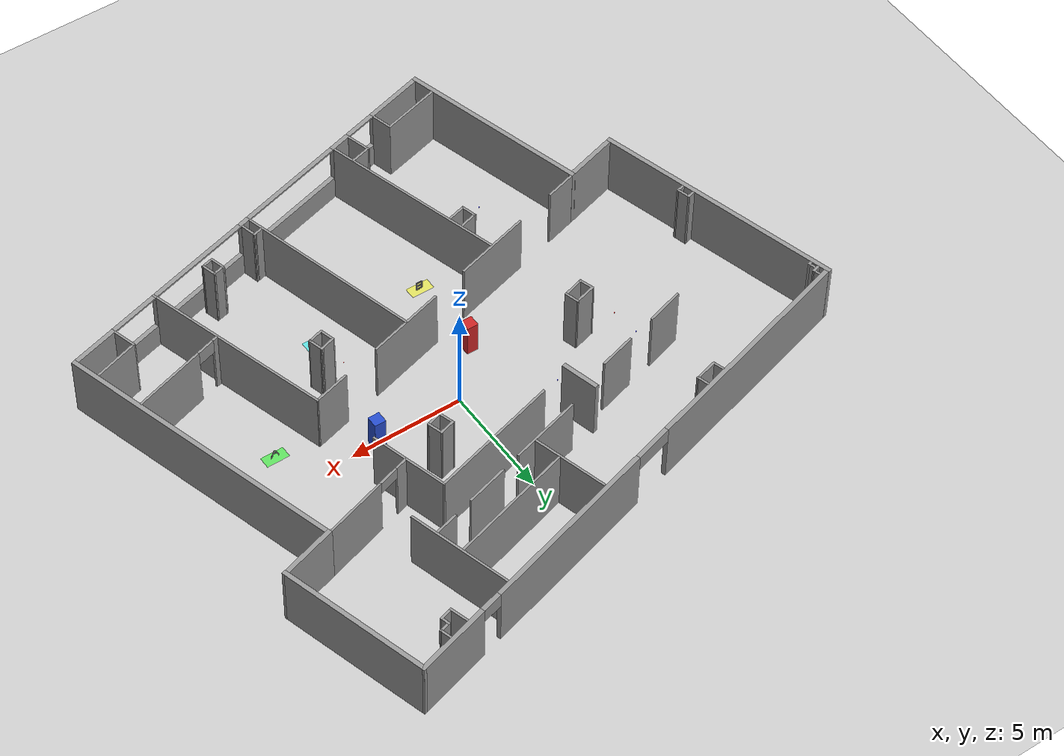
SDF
<sdf version="1.7">
 <world name="default">
  <plugin name="gazebo_ros_state" filename="libgazebo_ros_state.so">
   <ros>
    <namespace>/demo</namespace>
    <remapping>model_states:=model_states_demo</remapping>
    <remapping>link_states:=link_states_demo</remapping>
   </ros>
   <update_rate>1.0</update_rate>
  </plugin>
  <light name="sun" type="directional">
   <pose>0 0 10 0 -0 0</pose>
   <diffuse>0.8 0.8 0.8 1</diffuse>
   <specular>0.2 0.2 0.2 1</specular>
   <attenuation>
    <range>1000</range>
    <constant>0.9</constant>
    <linear>0.01</linear>
    <quadratic>0.001</quadratic>
   </attenuation>
   <direction>-0.5 0.1 -0.9</direction>
   <spot><inner_angle>0</inner_angle><outer_angle>0</outer_angle><falloff>0</falloff></spot>
  </light>
  <model name="ground_plane">
   <static>1</static>
   <link name="link">
    <collision name="collision">
     <geometry><plane><normal>0 0 1</normal><size>100 100</size></plane></geometry>
     <surface><friction><ode><mu>100</mu><mu2>100</mu2></ode></friction></surface>
    </collision>
    <visual name="visual">
     <cast_shadows>0</cast_shadows>
     <geometry><plane><normal>0 0 1</normal><size>100 100</size></plane></geometry>
     <material>
      <script><uri>file://media/materials/scripts/gazebo.material</uri><name>Gazebo/Grey</name></script>
     </material>
    </visual>
    <velocity_decay><linear>0</linear><angular>0</angular></velocity_decay>
   </link>
  </model>
  <physics type="ode">
   <ode>
    <solver>
     <type>quick</type>
     <iters>20</iters>
     <sor>1</sor>
     <use_dynamic_moi_rescaling>0</use_dynamic_moi_rescaling>
    </solver>
    <constraints>
     <cfm>0</cfm>
     <erp>0.2</erp>
     <contact_max_correcting_vel>100</contact_max_correcting_vel>
     <contact_surface_layer>0</contact_surface_layer>
    </constraints>
   </ode>
   <real_time_update_rate>1000</real_time_update_rate>
   <max_step_size>0.001</max_step_size>
   <real_time_factor>1</real_time_factor>
   <max_contacts>20</max_contacts>
  </physics>
  <scene><ambient>0.4 0.4 0.4 1</ambient><background>0.7 0.7 0.7 1</background><shadows>1</shadows></scene>
  <spherical_coordinates>
   <surface_model>EARTH_WGS84</surface_model>
   <latitude_deg>0</latitude_deg>
   <longitude_deg>0</longitude_deg>
   <elevation>0</elevation>
   <heading_deg>0</heading_deg>
  </spherical_coordinates>
  <model name="Move1">
   <pose>-1.82854 -2.00086 0.751454 0.001145 -0.005751 -2.6e-05</pose>
   <link name="link">
    <collision name="collision"><geometry><box><size>0.5 0.5 1.5</size></box></geometry></collision>
    <visual name="visual">
     <geometry><box><size>0.5 0.5 1.5</size></box></geometry>
     <material>
      <script><name>Red</name><uri>file://media/materials/scripts/gazebo.material</uri></script>
     </material>
    </visual>
    <inertial>
     <inertia><ixx>1</ixx><ixy>0</ixy><ixz>0</ixz><iyy>1</iyy><iyz>0</iyz><izz>1</izz></inertia>
     <mass>1</mass>
    </inertial>
   </link>
   <plugin name="move1_plugin" filename="/home/ros/dev_ws/src/yzbot/Move_Obs/build/libanimated_models.so"/>
  </model>
  <model name="Move2">
   <pose>3.81991 -0.000857 0.751454 0.001145 -0.005751 -2.6e-05</pose>
   <link name="link">
    <collision name="collision"><geometry><box><size>0.5 0.5 1.5</size></box></geometry></collision>
    <visual name="visual">
     <geometry><box><size>0.5 0.5 1.5</size></box></geometry>
     <material>
      <script><name>Blue</name><uri>file://media/materials/scripts/gazebo.material</uri></script>
     </material>
    </visual>
    <inertial>
     <inertia><ixx>1</ixx><ixy>0</ixy><ixz>0</ixz><iyy>1</iyy><iyz>0</iyz><izz>1</izz></inertia>
     <mass>1</mass>
    </inertial>
   </link>
   <plugin name="move1_plugin" filename="/home/ros/dev_ws/src/yzbot/Move_Obs/build/libanimated_models.so"/>
  </model>
  <model name="PAL_office">
   <pose>-1 -1 0 0 -0 0</pose>
   <link name="Wall_10">
    <collision name="Wall_10_Collision">
     <geometry><box><size>6.73478 0.2 2.78</size></box></geometry>
     <pose>0 0 1.39 0 -0 0</pose>
    </collision>
    <visual name="Wall_10_Visual">
     <pose>0 0 1.39 0 -0 0</pose>
     <geometry><box><size>6.73478 0.2 2.78</size></box></geometry>
     <material>
      <script><uri>file://media/materials/scripts/gazebo.material</uri><name>Gazebo/Grey</name></script>
      <ambient>0.5 0.5 0.5 1</ambient>
     </material>
    </visual>
    <pose>11.1005 9.10601 0 0 -0 1.85624</pose>
    <velocity_decay><linear>0</linear><angular>0</angular></velocity_decay>
   </link>
   <link name="Wall_101">
    <collision name="Wall_101_Collision">
     <geometry><box><size>0.35 0.1 2.78</size></box></geometry>
     <pose>0 0 1.39 0 -0 0</pose>
    </collision>
    <visual name="Wall_101_Visual">
     <pose>0 0 1.39 0 -0 0</pose>
     <geometry><box><size>0.35 0.1 2.78</size></box></geometry>
     <material>
      <script><uri>file://media/materials/scripts/gazebo.material</uri><name>Gazebo/Grey</name></script>
      <ambient>0.5 0.5 0.5 1</ambient>
     </material>
    </visual>
    <pose>-13.001 5.22701 0 0 0 -2.87429</pose>
    <velocity_decay><linear>0</linear><angular>0</angular></velocity_decay>
   </link>
   <link name="Wall_103">
    <collision name="Wall_103_Collision">
     <geometry><box><size>0.35 0.1 2.78</size></box></geometry>
     <pose>0 0 1.39 0 -0 0</pose>
    </collision>
    <visual name="Wall_103_Visual">
     <pose>0 0 1.39 0 -0 0</pose>
     <geometry><box><size>0.35 0.1 2.78</size></box></geometry>
     <material>
      <script><uri>file://media/materials/scripts/gazebo.material</uri><name>Gazebo/Grey</name></script>
      <ambient>0.5 0.5 0.5 1</ambient>
     </material>
    </visual>
    <pose>-12.915 5.38001 0 0 -0 1.85075</pose>
    <velocity_decay><linear>0</linear><angular>0</angular></velocity_decay>
   </link>
   <link name="Wall_113">
    <collision name="Wall_113_Collision">
     <geometry><box><size>0.183 0.1 2.78</size></box></geometry>
     <pose>0 0 1.39 0 -0 0</pose>
    </collision>
    <visual name="Wall_113_Visual">
     <pose>0 0 1.39 0 -0 0</pose>
     <geometry><box><size>0.183 0.1 2.78</size></box></geometry>
     <material>
      <script><uri>file://media/materials/scripts/gazebo.material</uri><name>Gazebo/Grey</name></script>
      <ambient>0.5 0.5 0.5 1</ambient>
     </material>
    </visual>
    <pose>-12.9885 4.88001 0 0 -0 0.268366</pose>
    <velocity_decay><linear>0</linear><angular>0</angular></velocity_decay>
   </link>
   <link name="Wall_118">
    <collision name="Wall_118_Collision">
     <geometry><box><size>0.252054 0.1 2.78</size></box></geometry>
     <pose>0 0 1.39 0 -0 0</pose>
    </collision>
    <visual name="Wall_118_Visual">
     <pose>0 0 1.39 0 -0 0</pose>
     <geometry><box><size>0.252054 0.1 2.78</size></box></geometry>
     <material>
      <script><uri>file://media/materials/scripts/gazebo.material</uri><name>Gazebo/Grey</name></script>
      <ambient>0.5 0.5 0.5 1</ambient>
     </material>
    </visual>
    <pose>-12.996 5.05551 0 0 0 -1.31147</pose>
    <velocity_decay><linear>0</linear><angular>0</angular></velocity_decay>
   </link>
   <link name="Wall_12">
    <collision name="Wall_12_Collision">
     <geometry><box><size>2.648 0.2 2.78</size></box></geometry>
     <pose>0 0 1.39 0 -0 0</pose>
    </collision>
    <visual name="Wall_12_Visual">
     <pose>0 0 1.39 0 -0 0</pose>
     <geometry><box><size>2.648 0.2 2.78</size></box></geometry>
     <material>
      <script><uri>file://media/materials/scripts/gazebo.material</uri><name>Gazebo/Grey</name></script>
      <ambient>0.5 0.5 0.5 1</ambient>
     </material>
    </visual>
    <pose>-9.23199 -4.61199 0 0 0 -2.8652</pose>
    <velocity_decay><linear>0</linear><angular>0</angular></velocity_decay>
   </link>
   <link name="Wall_121">
    <collision name="Wall_121_Collision">
     <geometry><box><size>1.01214 0.1 2.78</size></box></geometry>
     <pose>0 0 1.39 0 -0 0</pose>
    </collision>
    <visual name="Wall_121_Visual">
     <pose>0 0 1.39 0 -0 0</pose>
     <geometry><box><size>1.01214 0.1 2.78</size></box></geometry>
     <material>
      <script><uri>file://media/materials/scripts/gazebo.material</uri><name>Gazebo/Grey</name></script>
      <ambient>0.5 0.5 0.5 1</ambient>
     </material>
    </visual>
    <pose>-4.76149 1.21201 0 0 -0 0.266252</pose>
    <velocity_decay><linear>0</linear><angular>0</angular></velocity_decay>
   </link>
   <link name="Wall_122">
    <collision name="Wall_122_Collision">
     <geometry><box><size>0.660446 0.1 2.78</size></box></geometry>
     <pose>0 0 1.39 0 -0 0</pose>
    </collision>
    <visual name="Wall_122_Visual">
     <pose>0 0 1.39 0 -0 0</pose>
     <geometry><box><size>0.660446 0.1 2.78</size></box></geometry>
     <material>
      <script><uri>file://media/materials/scripts/gazebo.material</uri><name>Gazebo/Grey</name></script>
      <ambient>0.5 0.5 0.5 1</ambient>
     </material>
    </visual>
    <pose>-4.24649 1.06201 0 0 0 -1.29985</pose>
    <velocity_decay><linear>0</linear><angular>0</angular></velocity_decay>
   </link>
   <link name="Wall_127">
    <collision name="Wall_127_Collision">
     <geometry><box><size>0.678705 0.1 2.78</size></box></geometry>
     <pose>0 0 1.39 0 -0 0</pose>
    </collision>
    <visual name="Wall_127_Visual">
     <pose>0 0 1.39 0 -0 0</pose>
     <geometry><box><size>0.678705 0.1 2.78</size></box></geometry>
     <material>
      <script><uri>file://media/materials/scripts/gazebo.material</uri><name>Gazebo/Grey</name></script>
      <ambient>0.5 0.5 0.5 1</ambient>
     </material>
    </visual>
    <pose>-5.11149 0.817011 0 0 0 -1.25451</pose>
    <velocity_decay><linear>0</linear><angular>0</angular></velocity_decay>
   </link>
   <link name="Wall_128">
    <collision name="Wall_128_Collision">
     <geometry><box><size>0.913204 0.1 2.78</size></box></geometry>
     <pose>0 0 1.39 0 -0 0</pose>
    </collision>
    <visual name="Wall_128_Visual">
     <pose>0 0 1.39 0 -0 0</pose>
     <geometry><box><size>0.913204 0.1 2.78</size></box></geometry>
     <material>
      <script><uri>file://media/materials/scripts/gazebo.material</uri><name>Gazebo/Grey</name></script>
      <ambient>0.5 0.5 0.5 1</ambient>
     </material>
    </visual>
    <pose>-4.63149 0.657011 0 0 -0 0.286745</pose>
    <velocity_decay><linear>0</linear><angular>0</angular></velocity_decay>
   </link>
   <link name="Wall_133">
    <collision name="Wall_133_Collision">
     <geometry><box><size>0.754498 0.1 2.78</size></box></geometry>
     <pose>0 0 1.39 0 -0 0</pose>
    </collision>
    <visual name="Wall_133_Visual">
     <pose>0 0 1.39 0 -0 0</pose>
     <geometry><box><size>0.754498 0.1 2.78</size></box></geometry>
     <material>
      <script><uri>file://media/materials/scripts/gazebo.material</uri><name>Gazebo/Grey</name></script>
      <ambient>0.5 0.5 0.5 1</ambient>
     </material>
    </visual>
    <pose>3.37451 3.66401 0 0 -0 0.275362</pose>
    <velocity_decay><linear>0</linear><angular>0</angular></velocity_decay>
   </link>
   <link name="Wall_134">
    <collision name="Wall_134_Collision">
     <geometry><box><size>0.726947 0.1 2.78</size></box></geometry>
     <pose>0 0 1.39 0 -0 0</pose>
    </collision>
    <visual name="Wall_134_Visual">
     <pose>0 0 1.39 0 -0 0</pose>
     <geometry><box><size>0.726947 0.1 2.78</size></box></geometry>
     <material>
      <script><uri>file://media/materials/scripts/gazebo.material</uri><name>Gazebo/Grey</name></script>
      <ambient>0.5 0.5 0.5 1</ambient>
     </material>
    </visual>
    <pose>3.77951 3.45301 0 0 0 -1.27934</pose>
    <velocity_decay><linear>0</linear><angular>0</angular></velocity_decay>
   </link>
   <link name="Wall_14">
    <collision name="Wall_14_Collision">
     <geometry><box><size>8.475 0.2 2.78</size></box></geometry>
     <pose>0 0 1.39 0 -0 0</pose>
    </collision>
    <visual name="Wall_14_Visual">
     <pose>0 0 1.39 0 -0 0</pose>
     <geometry><box><size>8.475 0.2 2.78</size></box></geometry>
     <material>
      <script><uri>file://media/materials/scripts/gazebo.material</uri><name>Gazebo/Grey</name></script>
      <ambient>0.5 0.5 0.5 1</ambient>
     </material>
    </visual>
    <pose>-6.93049 -8.25999 0 0 0 -1.29568</pose>
    <velocity_decay><linear>0</linear><angular>0</angular></velocity_decay>
   </link>
   <link name="Wall_140">
    <collision name="Wall_140_Collision">
     <geometry><box><size>0.729033 0.1 2.78</size></box></geometry>
     <pose>0 0 1.39 0 -0 0</pose>
    </collision>
    <visual name="Wall_140_Visual">
     <pose>0 0 1.39 0 -0 0</pose>
     <geometry><box><size>0.729033 0.1 2.78</size></box></geometry>
     <material>
      <script><uri>file://media/materials/scripts/gazebo.material</uri><name>Gazebo/Grey</name></script>
      <ambient>0.5 0.5 0.5 1</ambient>
     </material>
    </visual>
    <pose>3.15251 3.27451 0 0 0 -1.27066</pose>
    <velocity_decay><linear>0</linear><angular>0</angular></velocity_decay>
   </link>
   <link name="Wall_142">
    <collision name="Wall_142_Collision">
     <geometry><box><size>0.721105 0.1 2.78</size></box></geometry>
     <pose>0 0 1.39 0 -0 0</pose>
    </collision>
    <visual name="Wall_142_Visual">
     <pose>0 0 1.39 0 -0 0</pose>
     <geometry><box><size>0.721105 0.1 2.78</size></box></geometry>
     <material>
      <script><uri>file://media/materials/scripts/gazebo.material</uri><name>Gazebo/Grey</name></script>
      <ambient>0.5 0.5 0.5 1</ambient>
     </material>
    </visual>
    <pose>3.57151 3.06601 0 0 0 -2.85754</pose>
    <velocity_decay><linear>0</linear><angular>0</angular></velocity_decay>
   </link>
   <link name="Wall_145">
    <collision name="Wall_145_Collision">
     <geometry><box><size>8.27375 0.1 2.78</size></box></geometry>
     <pose>0 0 1.39 0 -0 0</pose>
    </collision>
    <visual name="Wall_145_Visual">
     <pose>0 0 1.39 0 -0 0</pose>
     <geometry><box><size>8.27375 0.1 2.78</size></box></geometry>
     <material>
      <script><uri>file://media/materials/scripts/gazebo.material</uri><name>Gazebo/Grey</name></script>
      <ambient>0.5 0.5 0.5 1</ambient>
     </material>
    </visual>
    <pose>7.88901 -4.08549 0 0 0 -1.27598</pose>
    <velocity_decay><linear>0</linear><angular>0</angular></velocity_decay>
   </link>
   <link name="Wall_147">
    <collision name="Wall_147_Collision">
     <geometry><box><size>1.6624 0.1 2.78</size></box></geometry>
     <pose>0 0 1.39 0 -0 0</pose>
    </collision>
    <visual name="Wall_147_Visual">
     <pose>0 0 1.39 0 -0 0</pose>
     <geometry><box><size>1.6624 0.1 2.78</size></box></geometry>
     <material>
      <script><uri>file://media/materials/scripts/gazebo.material</uri><name>Gazebo/Grey</name></script>
      <ambient>0.5 0.5 0.5 1</ambient>
     </material>
    </visual>
    <pose>5.94751 -0.379989 0 0 0 -2.87613</pose>
    <velocity_decay><linear>0</linear><angular>0</angular></velocity_decay>
   </link>
   <link name="Wall_150">
    <pose>10.26 -4.39249 0 0 -0 0.289894</pose>
    <visual name="Wall_150_Visual_0">
     <pose>-2.03127 0 1.39 0 -0 0</pose>
     <geometry><box><size>0.2671 0.1 2.78</size></box></geometry>
     <material>
      <script><uri>file://media/materials/scripts/gazebo.material</uri><name>Gazebo/Grey</name></script>
      <ambient>0.5 0.5 0.5 1</ambient>
     </material>
    </visual>
    <collision name="Wall_150_Collision_0">
     <geometry><box><size>0.2671 0.1 2.78</size></box></geometry>
     <pose>-2.03127 0 1.39 0 -0 0</pose>
    </collision>
    <visual name="Wall_150_Visual_1">
     <pose>0.54355 0 1.39 0 -0 0</pose>
     <geometry><box><size>3.24255 0.1 2.78</size></box></geometry>
     <material>
      <script><uri>file://media/materials/scripts/gazebo.material</uri><name>Gazebo/Grey</name></script>
      <ambient>0.5 0.5 0.5 1</ambient>
     </material>
    </visual>
    <collision name="Wall_150_Collision_1">
     <geometry><box><size>3.24255 0.1 2.78</size></box></geometry>
     <pose>0.54355 0 1.39 0 -0 0</pose>
    </collision>
    <visual name="Wall_150_Visual_2">
     <pose>-1.48772 0 2.44 0 -0 0</pose>
     <geometry><box><size>0.82 0.1 0.68</size></box></geometry>
     <material>
      <script><uri>file://media/materials/scripts/gazebo.material</uri><name>Gazebo/Grey</name></script>
      <ambient>0.5 0.5 0.5 1</ambient>
     </material>
    </visual>
    <collision name="Wall_150_Collision_2">
     <geometry><box><size>0.82 0.1 0.68</size></box></geometry>
     <pose>-1.48772 0 2.44 0 -0 0</pose>
    </collision>
    <velocity_decay><linear>0</linear><angular>0</angular></velocity_decay>
   </link>
   <link name="Wall_153">
    <collision name="Wall_153_Collision">
     <geometry><box><size>2.08407 0.1 2.78</size></box></geometry>
     <pose>0 0 1.39 0 -0 0</pose>
    </collision>
    <visual name="Wall_153_Visual">
     <pose>0 0 1.39 0 -0 0</pose>
     <geometry><box><size>2.08407 0.1 2.78</size></box></geometry>
     <material>
      <script><uri>file://media/materials/scripts/gazebo.material</uri><name>Gazebo/Grey</name></script>
      <ambient>0.5 0.5 0.5 1</ambient>
     </material>
    </visual>
    <pose>11.9955 -6.18599 0 0 0 -2.85014</pose>
    <velocity_decay><linear>0</linear><angular>0</angular></velocity_decay>
   </link>
   <link name="Wall_154">
    <collision name="Wall_154_Collision">
     <geometry><box><size>1.04397 0.1 2.78</size></box></geometry>
     <pose>0 0 1.39 0 -0 0</pose>
    </collision>
    <visual name="Wall_154_Visual">
     <pose>0 0 1.39 0 -0 0</pose>
     <geometry><box><size>1.04397 0.1 2.78</size></box></geometry>
     <material>
      <script><uri>file://media/materials/scripts/gazebo.material</uri><name>Gazebo/Grey</name></script>
      <ambient>0.5 0.5 0.5 1</ambient>
     </material>
    </visual>
    <pose>11.176 -6.92449 0 0 0 -1.29061</pose>
    <velocity_decay><linear>0</linear><angular>0</angular></velocity_decay>
   </link>
   <link name="Wall_158">
    <collision name="Wall_158_Collision">
     <geometry><box><size>3.52366 0.1 2.78</size></box></geometry>
     <pose>0 0 1.39 0 -0 0</pose>
    </collision>
    <visual name="Wall_158_Visual">
     <pose>0 0 1.39 0 -0 0</pose>
     <geometry><box><size>3.52366 0.1 2.78</size></box></geometry>
     <material>
      <script><uri>file://media/materials/scripts/gazebo.material</uri><name>Gazebo/Grey</name></script>
      <ambient>0.5 0.5 0.5 1</ambient>
     </material>
    </visual>
    <pose>-3.20649 -2.89249 0 0 -0 0.269352</pose>
    <velocity_decay><linear>0</linear><angular>0</angular></velocity_decay>
   </link>
   <link name="Wall_16">
    <pose>3.78351 -9.59399 0 0 0 -2.87199</pose>
    <visual name="Wall_16_Visual_0">
     <pose>-8.83974 0 1.39 0 -0 0</pose>
     <geometry><box><size>2.04382 0.2 2.78</size></box></geometry>
     <material>
      <script><uri>file://media/materials/scripts/gazebo.material</uri><name>Gazebo/Grey</name></script>
      <ambient>0.5 0.5 0.5 1</ambient>
     </material>
    </visual>
    <collision name="Wall_16_Collision_0">
     <geometry><box><size>2.04382 0.2 2.78</size></box></geometry>
     <pose>-8.83974 0 1.39 0 -0 0</pose>
    </collision>
    <visual name="Wall_16_Visual_1">
     <pose>1.02191 0 0.55 0 -0 0</pose>
     <geometry><box><size>17.6795 0.2 1.1</size></box></geometry>
     <material>
      <script><uri>file://media/materials/scripts/gazebo.material</uri><name>Gazebo/Grey</name></script>
      <ambient>0.5 0.5 0.5 1</ambient>
     </material>
    </visual>
    <collision name="Wall_16_Collision_1">
     <geometry><box><size>17.6795 0.2 1.1</size></box></geometry>
     <pose>1.02191 0 0.55 0 -0 0</pose>
    </collision>
    <visual name="Wall_16_Visual_2">
     <pose>-5.54535 0 1.94 0 -0 0</pose>
     <geometry><box><size>0.100368 0.2 1.68</size></box></geometry>
     <material>
      <script><uri>file://media/materials/scripts/gazebo.material</uri><name>Gazebo/Grey</name></script>
      <ambient>0.5 0.5 0.5 1</ambient>
     </material>
    </visual>
    <collision name="Wall_16_Collision_2">
     <geometry><box><size>0.100368 0.2 1.68</size></box></geometry>
     <pose>-5.54535 0 1.94 0 -0 0</pose>
    </collision>
    <visual name="Wall_16_Visual_3">
     <pose>-0.435842 0 1.94 0 -0 0</pose>
     <geometry><box><size>0.509797 0.2 1.68</size></box></geometry>
     <material>
      <script><uri>file://media/materials/scripts/gazebo.material</uri><name>Gazebo/Grey</name></script>
      <ambient>0.5 0.5 0.5 1</ambient>
     </material>
    </visual>
    <collision name="Wall_16_Collision_3">
     <geometry><box><size>0.509797 0.2 1.68</size></box></geometry>
     <pose>-0.435842 0 1.94 0 -0 0</pose>
    </collision>
    <visual name="Wall_16_Visual_4">
     <pose>5.27686 0 1.94 0 -0 0</pose>
     <geometry><box><size>0.994619 0.2 1.68</size></box></geometry>
     <material>
      <script><uri>file://media/materials/scripts/gazebo.material</uri><name>Gazebo/Grey</name></script>
      <ambient>0.5 0.5 0.5 1</ambient>
     </material>
    </visual>
    <collision name="Wall_16_Collision_4">
     <geometry><box><size>0.994619 0.2 1.68</size></box></geometry>
     <pose>5.27686 0 1.94 0 -0 0</pose>
    </collision>
    <visual name="Wall_16_Visual_5">
     <pose>8.53741 0 1.94 0 -0 0</pose>
     <geometry><box><size>2.64848 0.2 1.68</size></box></geometry>
     <material>
      <script><uri>file://media/materials/scripts/gazebo.material</uri><name>Gazebo/Grey</name></script>
      <ambient>0.5 0.5 0.5 1</ambient>
     </material>
    </visual>
    <collision name="Wall_16_Collision_5">
     <geometry><box><size>2.64848 0.2 1.68</size></box></geometry>
     <pose>8.53741 0 1.94 0 -0 0</pose>
    </collision>
    <visual name="Wall_16_Visual_6">
     <pose>-6.70668 0 2.74 0 -0 0</pose>
     <geometry><box><size>2.22229 0.2 0.08</size></box></geometry>
     <material>
      <script><uri>file://media/materials/scripts/gazebo.material</uri><name>Gazebo/Grey</name></script>
      <ambient>0.5 0.5 0.5 1</ambient>
     </material>
    </visual>
    <collision name="Wall_16_Collision_6">
     <geometry><box><size>2.22229 0.2 0.08</size></box></geometry>
     <pose>-6.70668 0 2.74 0 -0 0</pose>
    </collision>
    <visual name="Wall_16_Visual_7">
     <pose>-3.09295 0 2.74 0 -0 0</pose>
     <geometry><box><size>4.80443 0.2 0.08</size></box></geometry>
     <material>
      <script><uri>file://media/materials/scripts/gazebo.material</uri><name>Gazebo/Grey</name></script>
      <ambient>0.5 0.5 0.5 1</ambient>
     </material>
    </visual>
    <collision name="Wall_16_Collision_7">
     <geometry><box><size>4.80443 0.2 0.08</size></box></geometry>
     <pose>-3.09295 0 2.74 0 -0 0</pose>
    </collision>
    <visual name="Wall_16_Visual_8">
     <pose>2.2993 0 2.74 0 -0 0</pose>
     <geometry><box><size>4.96049 0.2 0.08</size></box></geometry>
     <material>
      <script><uri>file://media/materials/scripts/gazebo.material</uri><name>Gazebo/Grey</name></script>
      <ambient>0.5 0.5 0.5 1</ambient>
     </material>
    </visual>
    <collision name="Wall_16_Collision_8">
     <geometry><box><size>4.96049 0.2 0.08</size></box></geometry>
     <pose>2.2993 0 2.74 0 -0 0</pose>
    </collision>
    <visual name="Wall_16_Visual_9">
     <pose>6.49367 0 2.74 0 -0 0</pose>
     <geometry><box><size>1.439 0.2 0.08</size></box></geometry>
     <material>
      <script><uri>file://media/materials/scripts/gazebo.material</uri><name>Gazebo/Grey</name></script>
      <ambient>0.5 0.5 0.5 1</ambient>
     </material>
    </visual>
    <collision name="Wall_16_Collision_9">
     <geometry><box><size>1.439 0.2 0.08</size></box></geometry>
     <pose>6.49367 0 2.74 0 -0 0</pose>
    </collision>
    <velocity_decay><linear>0</linear><angular>0</angular></velocity_decay>
   </link>
   <link name="Wall_160">
    <collision name="Wall_160_Collision">
     <geometry><box><size>3.56369 0.1 2.78</size></box></geometry>
     <pose>0 0 1.39 0 -0 0</pose>
    </collision>
    <visual name="Wall_160_Visual">
     <pose>0 0 1.39 0 -0 0</pose>
     <geometry><box><size>3.56369 0.1 2.78</size></box></geometry>
     <material>
      <script><uri>file://media/materials/scripts/gazebo.material</uri><name>Gazebo/Grey</name></script>
      <ambient>0.5 0.5 0.5 1</ambient>
     </material>
    </visual>
    <pose>1.79301 -1.50349 0 0 -0 0.269139</pose>
    <velocity_decay><linear>0</linear><angular>0</angular></velocity_decay>
   </link>
   <link name="Wall_162">
    <collision name="Wall_162_Collision">
     <geometry><box><size>1.39174 0.1 2.78</size></box></geometry>
     <pose>0 0 1.39 0 -0 0</pose>
    </collision>
    <visual name="Wall_162_Visual">
     <pose>0 0 1.39 0 -0 0</pose>
     <geometry><box><size>1.39174 0.1 2.78</size></box></geometry>
     <material>
      <script><uri>file://media/materials/scripts/gazebo.material</uri><name>Gazebo/Grey</name></script>
      <ambient>0.5 0.5 0.5 1</ambient>
     </material>
    </visual>
    <pose>-7.30849 -4.02049 0 0 0 -2.86808</pose>
    <velocity_decay><linear>0</linear><angular>0</angular></velocity_decay>
   </link>
   <link name="Wall_164">
    <collision name="Wall_164_Collision">
     <geometry><box><size>8.25895 0.1 2.78</size></box></geometry>
     <pose>0 0 1.39 0 -0 0</pose>
    </collision>
    <visual name="Wall_164_Visual">
     <pose>0 0 1.39 0 -0 0</pose>
     <geometry><box><size>8.25895 0.1 2.78</size></box></geometry>
     <material>
      <script><uri>file://media/materials/scripts/gazebo.material</uri><name>Gazebo/Grey</name></script>
      <ambient>0.5 0.5 0.5 1</ambient>
     </material>
    </visual>
    <pose>2.85601 -5.47899 0 0 0 -1.3012</pose>
    <velocity_decay><linear>0</linear><angular>0</angular></velocity_decay>
   </link>
   <link name="Wall_166">
    <collision name="Wall_166_Collision">
     <geometry><box><size>8.22 0.1 2.78</size></box></geometry>
     <pose>0 0 1.39 0 -0 0</pose>
    </collision>
    <visual name="Wall_166_Visual">
     <pose>0 0 1.39 0 -0 0</pose>
     <geometry><box><size>8.22 0.1 2.78</size></box></geometry>
     <material>
      <script><uri>file://media/materials/scripts/gazebo.material</uri><name>Gazebo/Grey</name></script>
      <ambient>0.5 0.5 0.5 1</ambient>
     </material>
    </visual>
    <pose>-2.06049 -6.85199 0 0 0 -1.28668</pose>
    <velocity_decay><linear>0</linear><angular>0</angular></velocity_decay>
   </link>
   <link name="Wall_168">
    <collision name="Wall_168_Collision">
     <geometry><box><size>0.743567 0.1 2.78</size></box></geometry>
     <pose>0 0 1.39 0 -0 0</pose>
    </collision>
    <visual name="Wall_168_Visual">
     <pose>0 0 1.39 0 -0 0</pose>
     <geometry><box><size>0.743567 0.1 2.78</size></box></geometry>
     <material>
      <script><uri>file://media/materials/scripts/gazebo.material</uri><name>Gazebo/Grey</name></script>
      <ambient>0.5 0.5 0.5 1</ambient>
     </material>
    </visual>
    <pose>4.88801 -2.31549 0 0 -0 0.288331</pose>
    <velocity_decay><linear>0</linear><angular>0</angular></velocity_decay>
   </link>
   <link name="Wall_169">
    <collision name="Wall_169_Collision">
     <geometry><box><size>0.700613 0.1 2.78</size></box></geometry>
     <pose>0 0 1.39 0 -0 0</pose>
    </collision>
    <visual name="Wall_169_Visual">
     <pose>0 0 1.39 0 -0 0</pose>
     <geometry><box><size>0.700613 0.1 2.78</size></box></geometry>
     <material>
      <script><uri>file://media/materials/scripts/gazebo.material</uri><name>Gazebo/Grey</name></script>
      <ambient>0.5 0.5 0.5 1</ambient>
     </material>
    </visual>
    <pose>5.27451 -2.51399 0 0 0 -1.30805</pose>
    <velocity_decay><linear>0</linear><angular>0</angular></velocity_decay>
   </link>
   <link name="Wall_171">
    <collision name="Wall_171_Collision">
     <geometry><box><size>0.699643 0.1 2.78</size></box></geometry>
     <pose>0 0 1.39 0 -0 0</pose>
    </collision>
    <visual name="Wall_171_Visual">
     <pose>0 0 1.39 0 -0 0</pose>
     <geometry><box><size>0.699643 0.1 2.78</size></box></geometry>
     <material>
      <script><uri>file://media/materials/scripts/gazebo.material</uri><name>Gazebo/Grey</name></script>
      <ambient>0.5 0.5 0.5 1</ambient>
     </material>
    </visual>
    <pose>4.65701 -2.69649 0 0 0 -1.30923</pose>
    <velocity_decay><linear>0</linear><angular>0</angular></velocity_decay>
   </link>
   <link name="Wall_172">
    <collision name="Wall_172_Collision">
     <geometry><box><size>0.74415 0.1 2.78</size></box></geometry>
     <pose>0 0 1.39 0 -0 0</pose>
    </collision>
    <visual name="Wall_172_Visual">
     <pose>0 0 1.39 0 -0 0</pose>
     <geometry><box><size>0.74415 0.1 2.78</size></box></geometry>
     <material>
      <script><uri>file://media/materials/scripts/gazebo.material</uri><name>Gazebo/Grey</name></script>
      <ambient>0.5 0.5 0.5 1</ambient>
     </material>
    </visual>
    <pose>5.04351 -2.89499 0 0 -0 0.286402</pose>
    <velocity_decay><linear>0</linear><angular>0</angular></velocity_decay>
   </link>
   <link name="Wall_178">
    <collision name="Wall_178_Collision">
     <geometry><box><size>0.577966 0.1 2.78</size></box></geometry>
     <pose>0 0 1.39 0 -0 0</pose>
    </collision>
    <visual name="Wall_178_Visual">
     <pose>0 0 1.39 0 -0 0</pose>
     <geometry><box><size>0.577966 0.1 2.78</size></box></geometry>
     <material>
      <script><uri>file://media/materials/scripts/gazebo.material</uri><name>Gazebo/Grey</name></script>
      <ambient>0.5 0.5 0.5 1</ambient>
     </material>
    </visual>
    <pose>6.36001 -7.86249 0 0 0 -2.89002</pose>
    <velocity_decay><linear>0</linear><angular>0</angular></velocity_decay>
   </link>
   <link name="Wall_179">
    <collision name="Wall_179_Collision">
     <geometry><box><size>0.699835 0.1 2.78</size></box></geometry>
     <pose>0 0 1.39 0 -0 0</pose>
    </collision>
    <visual name="Wall_179_Visual">
     <pose>0 0 1.39 0 -0 0</pose>
     <geometry><box><size>0.699835 0.1 2.78</size></box></geometry>
     <material>
      <script><uri>file://media/materials/scripts/gazebo.material</uri><name>Gazebo/Grey</name></script>
      <ambient>0.5 0.5 0.5 1</ambient>
     </material>
    </visual>
    <pose>6.20601 -8.21149 0 0 0 -1.30923</pose>
    <velocity_decay><linear>0</linear><angular>0</angular></velocity_decay>
   </link>
   <link name="Wall_181">
    <collision name="Wall_181_Collision">
     <geometry><box><size>0.699779 0.1 2.78</size></box></geometry>
     <pose>0 0 1.39 0 -0 0</pose>
    </collision>
    <visual name="Wall_181_Visual">
     <pose>0 0 1.39 0 -0 0</pose>
     <geometry><box><size>0.699779 0.1 2.78</size></box></geometry>
     <material>
      <script><uri>file://media/materials/scripts/gazebo.material</uri><name>Gazebo/Grey</name></script>
      <ambient>0.5 0.5 0.5 1</ambient>
     </material>
    </visual>
    <pose>6.66901 -8.09249 0 0 0 -1.30923</pose>
    <velocity_decay><linear>0</linear><angular>0</angular></velocity_decay>
   </link>
   <link name="Wall_182">
    <collision name="Wall_182_Collision">
     <geometry><box><size>0.578048 0.1 2.78</size></box></geometry>
     <pose>0 0 1.39 0 -0 0</pose>
    </collision>
    <visual name="Wall_182_Visual">
     <pose>0 0 1.39 0 -0 0</pose>
     <geometry><box><size>0.578048 0.1 2.78</size></box></geometry>
     <material>
      <script><uri>file://media/materials/scripts/gazebo.material</uri><name>Gazebo/Grey</name></script>
      <ambient>0.5 0.5 0.5 1</ambient>
     </material>
    </visual>
    <pose>6.51501 -8.44149 0 0 0 -2.89002</pose>
    <velocity_decay><linear>0</linear><angular>0</angular></velocity_decay>
   </link>
   <link name="Wall_185">
    <collision name="Wall_185_Collision">
     <geometry><box><size>0.75 0.1 2.78</size></box></geometry>
     <pose>0 0 1.39 0 -0 0</pose>
    </collision>
    <visual name="Wall_185_Visual">
     <pose>0 0 1.39 0 -0 0</pose>
     <geometry><box><size>0.75 0.1 2.78</size></box></geometry>
     <material>
      <script><uri>file://media/materials/scripts/gazebo.material</uri><name>Gazebo/Grey</name></script>
      <ambient>0.5 0.5 0.5 1</ambient>
     </material>
    </visual>
    <pose>4.28501 -8.98999 0 0 0 -1.3206</pose>
    <velocity_decay><linear>0</linear><angular>0</angular></velocity_decay>
   </link>
   <link name="Wall_189">
    <collision name="Wall_189_Collision">
     <geometry><box><size>0.478287 0.1 2.78</size></box></geometry>
     <pose>0 0 1.39 0 -0 0</pose>
    </collision>
    <visual name="Wall_189_Visual">
     <pose>0 0 1.39 0 -0 0</pose>
     <geometry><box><size>0.478287 0.1 2.78</size></box></geometry>
     <material>
      <script><uri>file://media/materials/scripts/gazebo.material</uri><name>Gazebo/Grey</name></script>
      <ambient>0.5 0.5 0.5 1</ambient>
     </material>
    </visual>
    <pose>4.02201 -8.72399 0 0 0 -2.87929</pose>
    <velocity_decay><linear>0</linear><angular>0</angular></velocity_decay>
   </link>
   <link name="Wall_191">
    <collision name="Wall_191_Collision">
     <geometry><box><size>2.70029 0.1 2.78</size></box></geometry>
     <pose>0 0 1.39 0 -0 0</pose>
    </collision>
    <visual name="Wall_191_Visual">
     <pose>0 0 1.39 0 -0 0</pose>
     <geometry><box><size>2.70029 0.1 2.78</size></box></geometry>
     <material>
      <script><uri>file://media/materials/scripts/gazebo.material</uri><name>Gazebo/Grey</name></script>
      <ambient>0.5 0.5 0.5 1</ambient>
     </material>
    </visual>
    <pose>-4.71249 -10.9095 0 0 -0 0.261767</pose>
    <velocity_decay><linear>0</linear><angular>0</angular></velocity_decay>
   </link>
   <link name="Wall_192">
    <collision name="Wall_192_Collision">
     <geometry><box><size>0.952808 0.1 2.78</size></box></geometry>
     <pose>0 0 1.39 0 -0 0</pose>
    </collision>
    <visual name="Wall_192_Visual">
     <pose>0 0 1.39 0 -0 0</pose>
     <geometry><box><size>0.952808 0.1 2.78</size></box></geometry>
     <material>
      <script><uri>file://media/materials/scripts/gazebo.material</uri><name>Gazebo/Grey</name></script>
      <ambient>0.5 0.5 0.5 1</ambient>
     </material>
    </visual>
    <pose>-3.34599 -10.985 0 0 0 -1.30876</pose>
    <velocity_decay><linear>0</linear><angular>0</angular></velocity_decay>
   </link>
   <link name="Wall_194">
    <collision name="Wall_194_Collision">
     <geometry><box><size>0.950031 0.1 2.78</size></box></geometry>
     <pose>0 0 1.39 0 -0 0</pose>
    </collision>
    <visual name="Wall_194_Visual">
     <pose>0 0 1.39 0 -0 0</pose>
     <geometry><box><size>0.950031 0.1 2.78</size></box></geometry>
     <material>
      <script><uri>file://media/materials/scripts/gazebo.material</uri><name>Gazebo/Grey</name></script>
      <ambient>0.5 0.5 0.5 1</ambient>
     </material>
    </visual>
    <pose>-1.62899 -9.93999 0 0 -0 0.261815</pose>
    <velocity_decay><linear>0</linear><angular>0</angular></velocity_decay>
   </link>
   <link name="Wall_196">
    <collision name="Wall_196_Collision">
     <geometry><box><size>1.08791 0.1 2.78</size></box></geometry>
     <pose>0 0 1.39 0 -0 0</pose>
    </collision>
    <visual name="Wall_196_Visual">
     <pose>0 0 1.39 0 -0 0</pose>
     <geometry><box><size>1.08791 0.1 2.78</size></box></geometry>
     <material>
      <script><uri>file://media/materials/scripts/gazebo.material</uri><name>Gazebo/Grey</name></script>
      <ambient>0.5 0.5 0.5 1</ambient>
     </material>
    </visual>
    <pose>-1.90449 -10.525 0 0 0 -1.29389</pose>
    <velocity_decay><linear>0</linear><angular>0</angular></velocity_decay>
   </link>
   <link name="Wall_200">
    <collision name="Wall_200_Collision">
     <geometry><box><size>0.699598 0.1 2.78</size></box></geometry>
     <pose>0 0 1.39 0 -0 0</pose>
    </collision>
    <visual name="Wall_200_Visual">
     <pose>0 0 1.39 0 -0 0</pose>
     <geometry><box><size>0.699598 0.1 2.78</size></box></geometry>
     <material>
      <script><uri>file://media/materials/scripts/gazebo.material</uri><name>Gazebo/Grey</name></script>
      <ambient>0.5 0.5 0.5 1</ambient>
     </material>
    </visual>
    <pose>-3.48749 -4.94449 0 0 0 -1.30762</pose>
    <velocity_decay><linear>0</linear><angular>0</angular></velocity_decay>
   </link>
   <link name="Wall_202">
    <collision name="Wall_202_Collision">
     <geometry><box><size>0.838717 0.1 2.78</size></box></geometry>
     <pose>0 0 1.39 0 -0 0</pose>
    </collision>
    <visual name="Wall_202_Visual">
     <pose>0 0 1.39 0 -0 0</pose>
     <geometry><box><size>0.838717 0.1 2.78</size></box></geometry>
     <material>
      <script><uri>file://media/materials/scripts/gazebo.material</uri><name>Gazebo/Grey</name></script>
      <ambient>0.5 0.5 0.5 1</ambient>
     </material>
    </visual>
    <pose>-3.21049 -4.55299 0 0 -0 0.279787</pose>
    <velocity_decay><linear>0</linear><angular>0</angular></velocity_decay>
   </link>
   <link name="Wall_204">
    <collision name="Wall_204_Collision">
     <geometry><box><size>0.862099 0.1 2.78</size></box></geometry>
     <pose>0 0 1.39 0 -0 0</pose>
    </collision>
    <visual name="Wall_204_Visual">
     <pose>0 0 1.39 0 -0 0</pose>
     <geometry><box><size>0.862099 0.1 2.78</size></box></geometry>
     <material>
      <script><uri>file://media/materials/scripts/gazebo.material</uri><name>Gazebo/Grey</name></script>
      <ambient>0.5 0.5 0.5 1</ambient>
     </material>
    </visual>
    <pose>-3.04199 -5.13399 0 0 -0 0.265676</pose>
    <velocity_decay><linear>0</linear><angular>0</angular></velocity_decay>
   </link>
   <link name="Wall_21">
    <collision name="Wall_21_Collision">
     <geometry><box><size>2.596 0.2 2.78</size></box></geometry>
     <pose>0 0 1.39 0 -0 0</pose>
    </collision>
    <visual name="Wall_21_Visual">
     <pose>0 0 1.39 0 -0 0</pose>
     <geometry><box><size>2.596 0.2 2.78</size></box></geometry>
     <material>
      <script><uri>file://media/materials/scripts/gazebo.material</uri><name>Gazebo/Grey</name></script>
      <ambient>0.5 0.5 0.5 1</ambient>
     </material>
    </visual>
    <pose>10.873 5.62701 0 0 0 -2.85034</pose>
    <velocity_decay><linear>0</linear><angular>0</angular></velocity_decay>
   </link>
   <link name="Wall_28">
    <collision name="Wall_28_Collision">
     <geometry><box><size>12.756 0.2 2.78</size></box></geometry>
     <pose>0 0 1.39 0 -0 0</pose>
    </collision>
    <visual name="Wall_28_Visual">
     <pose>0 0 1.39 0 -0 0</pose>
     <geometry><box><size>12.756 0.2 2.78</size></box></geometry>
     <material>
      <script><uri>file://media/materials/scripts/gazebo.material</uri><name>Gazebo/Grey</name></script>
      <ambient>0.5 0.5 0.5 1</ambient>
     </material>
    </visual>
    <pose>11.575 -0.925489 0 0 -0 1.86035</pose>
    <velocity_decay><linear>0</linear><angular>0</angular></velocity_decay>
   </link>
   <link name="Wall_33">
    <collision name="Wall_33_Collision">
     <geometry><box><size>1.65613 0.2 2.78</size></box></geometry>
     <pose>0 0 1.39 0 -0 0</pose>
    </collision>
    <visual name="Wall_33_Visual">
     <pose>0 0 1.39 0 -0 0</pose>
     <geometry><box><size>1.65613 0.2 2.78</size></box></geometry>
     <material>
      <script><uri>file://media/materials/scripts/gazebo.material</uri><name>Gazebo/Grey</name></script>
      <ambient>0.5 0.5 0.5 1</ambient>
     </material>
    </visual>
    <pose>-2.22699 4.43951 0 0 0 -1.31033</pose>
    <velocity_decay><linear>0</linear><angular>0</angular></velocity_decay>
   </link>
   <link name="Wall_38">
    <collision name="Wall_38_Collision">
     <geometry><box><size>0.558077 0.1 2.78</size></box></geometry>
     <pose>0 0 1.39 0 -0 0</pose>
    </collision>
    <visual name="Wall_38_Visual">
     <pose>0 0 1.39 0 -0 0</pose>
     <geometry><box><size>0.558077 0.1 2.78</size></box></geometry>
     <material>
      <script><uri>file://media/materials/scripts/gazebo.material</uri><name>Gazebo/Grey</name></script>
      <ambient>0.5 0.5 0.5 1</ambient>
     </material>
    </visual>
    <pose>-5.93999 7.27151 0 0 0 -1.29459</pose>
    <velocity_decay><linear>0</linear><angular>0</angular></velocity_decay>
   </link>
   <link name="Wall_39">
    <collision name="Wall_39_Collision">
     <geometry><box><size>1.06 0.1 2.78</size></box></geometry>
     <pose>0 0 1.39 0 -0 0</pose>
    </collision>
    <visual name="Wall_39_Visual">
     <pose>0 0 1.39 0 -0 0</pose>
     <geometry><box><size>1.06 0.1 2.78</size></box></geometry>
     <material>
      <script><uri>file://media/materials/scripts/gazebo.material</uri><name>Gazebo/Grey</name></script>
      <ambient>0.5 0.5 0.5 1</ambient>
     </material>
    </visual>
    <pose>-6.34099 6.92601 0 0 0 -2.87817</pose>
    <velocity_decay><linear>0</linear><angular>0</angular></velocity_decay>
   </link>
   <link name="Wall_4">
    <collision name="Wall_4_Collision">
     <geometry><box><size>11.09 0.2 2.78</size></box></geometry>
     <pose>0 0 1.39 0 -0 0</pose>
    </collision>
    <visual name="Wall_4_Visual">
     <pose>0 0 1.39 0 -0 0</pose>
     <geometry><box><size>11.09 0.2 2.78</size></box></geometry>
     <material>
      <script><uri>file://media/materials/scripts/gazebo.material</uri><name>Gazebo/Grey</name></script>
      <ambient>0.5 0.5 0.5 1</ambient>
     </material>
    </visual>
    <pose>-11.889 0.294011 0 0 -0 1.84598</pose>
    <velocity_decay><linear>0</linear><angular>0</angular></velocity_decay>
   </link>
   <link name="Wall_40">
    <collision name="Wall_40_Collision">
     <geometry><box><size>0.538963 0.1 2.78</size></box></geometry>
     <pose>0 0 1.39 0 -0 0</pose>
    </collision>
    <visual name="Wall_40_Visual">
     <pose>0 0 1.39 0 -0 0</pose>
     <geometry><box><size>0.538963 0.1 2.78</size></box></geometry>
     <material>
      <script><uri>file://media/materials/scripts/gazebo.material</uri><name>Gazebo/Grey</name></script>
      <ambient>0.5 0.5 0.5 1</ambient>
     </material>
    </visual>
    <pose>-6.86699 7.01151 0 0 -0 1.85942</pose>
    <velocity_decay><linear>0</linear><angular>0</angular></velocity_decay>
   </link>
   <link name="Wall_43">
    <collision name="Wall_43_Collision">
     <geometry><box><size>3.24124 0.1 2.78</size></box></geometry>
     <pose>0 0 1.39 0 -0 0</pose>
    </collision>
    <visual name="Wall_43_Visual">
     <pose>0 0 1.39 0 -0 0</pose>
     <geometry><box><size>3.24124 0.1 2.78</size></box></geometry>
     <material>
      <script><uri>file://media/materials/scripts/gazebo.material</uri><name>Gazebo/Grey</name></script>
      <ambient>0.5 0.5 0.5 1</ambient>
     </material>
    </visual>
    <pose>0.389508 5.84601 0 0 -0 0.267369</pose>
    <velocity_decay><linear>0</linear><angular>0</angular></velocity_decay>
   </link>
   <link name="Wall_45">
    <collision name="Wall_45_Collision">
     <geometry><box><size>1.91692 0.1 2.78</size></box></geometry>
     <pose>0 0 1.39 0 -0 0</pose>
    </collision>
    <visual name="Wall_45_Visual">
     <pose>0 0 1.39 0 -0 0</pose>
     <geometry><box><size>1.91692 0.1 2.78</size></box></geometry>
     <material>
      <script><uri>file://media/materials/scripts/gazebo.material</uri><name>Gazebo/Grey</name></script>
      <ambient>0.5 0.5 0.5 1</ambient>
     </material>
    </visual>
    <pose>3.68951 6.76601 0 0 -0 0.273009</pose>
    <velocity_decay><linear>0</linear><angular>0</angular></velocity_decay>
   </link>
   <link name="Wall_47">
    <collision name="Wall_47_Collision">
     <geometry><box><size>1.06 0.1 2.78</size></box></geometry>
     <pose>0 0 1.39 0 -0 0</pose>
    </collision>
    <visual name="Wall_47_Visual">
     <pose>0 0 1.39 0 -0 0</pose>
     <geometry><box><size>1.06 0.1 2.78</size></box></geometry>
     <material>
      <script><uri>file://media/materials/scripts/gazebo.material</uri><name>Gazebo/Grey</name></script>
      <ambient>0.5 0.5 0.5 1</ambient>
     </material>
    </visual>
    <pose>5.92701 7.39951 0 0 -0 0.271003</pose>
    <velocity_decay><linear>0</linear><angular>0</angular></velocity_decay>
   </link>
   <link name="Wall_50">
    <collision name="Wall_50_Collision">
     <geometry><box><size>4.61888 0.1 2.78</size></box></geometry>
     <pose>0 0 1.39 0 -0 0</pose>
    </collision>
    <visual name="Wall_50_Visual">
     <pose>0 0 1.39 0 -0 0</pose>
     <geometry><box><size>4.61888 0.1 2.78</size></box></geometry>
     <material>
      <script><uri>file://media/materials/scripts/gazebo.material</uri><name>Gazebo/Grey</name></script>
      <ambient>0.5 0.5 0.5 1</ambient>
     </material>
    </visual>
    <pose>6.18151 8.60301 0 0 -0 1.85013</pose>
    <velocity_decay><linear>0</linear><angular>0</angular></velocity_decay>
   </link>
   <link name="Wall_52">
    <collision name="Wall_52_Collision">
     <geometry><box><size>3.325 0.1 2.78</size></box></geometry>
     <pose>0 0 1.39 0 -0 0</pose>
    </collision>
    <visual name="Wall_52_Visual">
     <pose>0 0 1.39 0 -0 0</pose>
     <geometry><box><size>3.325 0.1 2.78</size></box></geometry>
     <material>
      <script><uri>file://media/materials/scripts/gazebo.material</uri><name>Gazebo/Grey</name></script>
      <ambient>0.5 0.5 0.5 1</ambient>
     </material>
    </visual>
    <pose>0.530508 7.64401 0 0 -0 1.84586</pose>
    <velocity_decay><linear>0</linear><angular>0</angular></velocity_decay>
   </link>
   <link name="Wall_54">
    <collision name="Wall_54_Collision">
     <geometry><box><size>5.612 0.1 2.78</size></box></geometry>
     <pose>0 0 1.39 0 -0 0</pose>
    </collision>
    <visual name="Wall_54_Visual">
     <pose>0 0 1.39 0 -0 0</pose>
     <geometry><box><size>5.612 0.1 2.78</size></box></geometry>
     <material>
      <script><uri>file://media/materials/scripts/gazebo.material</uri><name>Gazebo/Grey</name></script>
      <ambient>0.5 0.5 0.5 1</ambient>
     </material>
    </visual>
    <pose>3.39901 7.96351 0 0 -0 0.27653</pose>
    <velocity_decay><linear>0</linear><angular>0</angular></velocity_decay>
   </link>
   <link name="Wall_59">
    <collision name="Wall_59_Collision">
     <geometry><box><size>0.857773 0.1 2.78</size></box></geometry>
     <pose>0 0 1.39 0 -0 0</pose>
    </collision>
    <visual name="Wall_59_Visual">
     <pose>0 0 1.39 0 -0 0</pose>
     <geometry><box><size>0.857773 0.1 2.78</size></box></geometry>
     <material>
      <script><uri>file://media/materials/scripts/gazebo.material</uri><name>Gazebo/Grey</name></script>
      <ambient>0.5 0.5 0.5 1</ambient>
     </material>
    </visual>
    <pose>7.85401 11.0345 0 0 0 -1.27744</pose>
    <velocity_decay><linear>0</linear><angular>0</angular></velocity_decay>
   </link>
   <link name="Wall_6">
    <pose>-1.49949 8.91251 0 0 0 -2.86398</pose>
    <visual name="Wall_6_Visual_0">
     <pose>-10.5551 0 1.39 0 -0 0</pose>
     <geometry><box><size>3.37984 0.2 2.78</size></box></geometry>
     <material>
      <script><uri>file://media/materials/scripts/gazebo.material</uri><name>Gazebo/Grey</name></script>
      <ambient>0.5 0.5 0.5 1</ambient>
     </material>
    </visual>
    <collision name="Wall_6_Collision_0">
     <geometry><box><size>3.37984 0.2 2.78</size></box></geometry>
     <pose>-10.5551 0 1.39 0 -0 0</pose>
    </collision>
    <visual name="Wall_6_Visual_1">
     <pose>-3.85518 0 1.39 0 -0 0</pose>
     <geometry><box><size>8.17996 0.2 2.78</size></box></geometry>
     <material>
      <script><uri>file://media/materials/scripts/gazebo.material</uri><name>Gazebo/Grey</name></script>
      <ambient>0.5 0.5 0.5 1</ambient>
     </material>
    </visual>
    <collision name="Wall_6_Collision_1">
     <geometry><box><size>8.17996 0.2 2.78</size></box></geometry>
     <pose>-3.85518 0 1.39 0 -0 0</pose>
    </collision>
    <visual name="Wall_6_Visual_2">
     <pose>7.1049 0 1.39 0 -0 0</pose>
     <geometry><box><size>10.2802 0.2 2.78</size></box></geometry>
     <material>
      <script><uri>file://media/materials/scripts/gazebo.material</uri><name>Gazebo/Grey</name></script>
      <ambient>0.5 0.5 0.5 1</ambient>
     </material>
    </visual>
    <collision name="Wall_6_Collision_2">
     <geometry><box><size>10.2802 0.2 2.78</size></box></geometry>
     <pose>7.1049 0 1.39 0 -0 0</pose>
    </collision>
    <visual name="Wall_6_Visual_3">
     <pose>1.0998 0 2.415 0 -0 0</pose>
     <geometry><box><size>1.73 0.2 0.73</size></box></geometry>
     <material>
      <script><uri>file://media/materials/scripts/gazebo.material</uri><name>Gazebo/Grey</name></script>
      <ambient>0.5 0.5 0.5 1</ambient>
     </material>
    </visual>
    <collision name="Wall_6_Collision_3">
     <geometry><box><size>1.73 0.2 0.73</size></box></geometry>
     <pose>1.0998 0 2.415 0 -0 0</pose>
    </collision>
    <visual name="Wall_6_Visual_4">
     <pose>-8.40516 0 2.44 0 -0 0</pose>
     <geometry><box><size>0.92 0.2 0.68</size></box></geometry>
     <material>
      <script><uri>file://media/materials/scripts/gazebo.material</uri><name>Gazebo/Grey</name></script>
      <ambient>0.5 0.5 0.5 1</ambient>
     </material>
    </visual>
    <collision name="Wall_6_Collision_4">
     <geometry><box><size>0.92 0.2 0.68</size></box></geometry>
     <pose>-8.40516 0 2.44 0 -0 0</pose>
    </collision>
    <velocity_decay><linear>0</linear><angular>0</angular></velocity_decay>
   </link>
   <link name="Wall_60">
    <collision name="Wall_60_Collision">
     <geometry><box><size>0.61465 0.1 2.78</size></box></geometry>
     <pose>0 0 1.39 0 -0 0</pose>
    </collision>
    <visual name="Wall_60_Visual">
     <pose>0 0 1.39 0 -0 0</pose>
     <geometry><box><size>0.61465 0.1 2.78</size></box></geometry>
     <material>
      <script><uri>file://media/materials/scripts/gazebo.material</uri><name>Gazebo/Grey</name></script>
      <ambient>0.5 0.5 0.5 1</ambient>
     </material>
    </visual>
    <pose>8.20951 10.7475 0 0 -0 0.297785</pose>
    <velocity_decay><linear>0</linear><angular>0</angular></velocity_decay>
   </link>
   <link name="Wall_61">
    <collision name="Wall_61_Collision">
     <geometry><box><size>0.435541 0.1 2.78</size></box></geometry>
     <pose>0 0 1.39 0 -0 0</pose>
    </collision>
    <visual name="Wall_61_Visual">
     <pose>0 0 1.39 0 -0 0</pose>
     <geometry><box><size>0.435541 0.1 2.78</size></box></geometry>
     <material>
      <script><uri>file://media/materials/scripts/gazebo.material</uri><name>Gazebo/Grey</name></script>
      <ambient>0.5 0.5 0.5 1</ambient>
     </material>
    </visual>
    <pose>8.41351 10.9855 0 0 -0 1.82372</pose>
    <velocity_decay><linear>0</linear><angular>0</angular></velocity_decay>
   </link>
   <link name="Wall_62">
    <collision name="Wall_62_Collision">
     <geometry><box><size>0.514773 0.1 2.78</size></box></geometry>
     <pose>0 0 1.39 0 -0 0</pose>
    </collision>
    <visual name="Wall_62_Visual">
     <pose>0 0 1.39 0 -0 0</pose>
     <geometry><box><size>0.514773 0.1 2.78</size></box></geometry>
     <material>
      <script><uri>file://media/materials/scripts/gazebo.material</uri><name>Gazebo/Grey</name></script>
      <ambient>0.5 0.5 0.5 1</ambient>
     </material>
    </visual>
    <pose>8.57201 11.201 0 0 -0 0.258428</pose>
    <velocity_decay><linear>0</linear><angular>0</angular></velocity_decay>
   </link>
   <link name="Wall_63">
    <collision name="Wall_63_Collision">
     <geometry><box><size>0.530853 0.1 2.78</size></box></geometry>
     <pose>0 0 1.39 0 -0 0</pose>
    </collision>
    <visual name="Wall_63_Visual">
     <pose>0 0 1.39 0 -0 0</pose>
     <geometry><box><size>0.530853 0.1 2.78</size></box></geometry>
     <material>
      <script><uri>file://media/materials/scripts/gazebo.material</uri><name>Gazebo/Grey</name></script>
      <ambient>0.5 0.5 0.5 1</ambient>
     </material>
    </visual>
    <pose>8.71601 11.462 0 0 -0 1.83603</pose>
    <velocity_decay><linear>0</linear><angular>0</angular></velocity_decay>
   </link>
   <link name="Wall_65">
    <collision name="Wall_65_Collision">
     <geometry><box><size>5.92278 0.1 2.78</size></box></geometry>
     <pose>0 0 1.39 0 -0 0</pose>
    </collision>
    <visual name="Wall_65_Visual">
     <pose>0 0 1.39 0 -0 0</pose>
     <geometry><box><size>5.92278 0.1 2.78</size></box></geometry>
     <material>
      <script><uri>file://media/materials/scripts/gazebo.material</uri><name>Gazebo/Grey</name></script>
      <ambient>0.5 0.5 0.5 1</ambient>
     </material>
    </visual>
    <pose>2.17451 5.04351 0 0 -0 0.269641</pose>
    <velocity_decay><linear>0</linear><angular>0</angular></velocity_decay>
   </link>
   <link name="Wall_66">
    <collision name="Wall_66_Collision">
     <geometry><box><size>3.49145 0.1 2.78</size></box></geometry>
     <pose>0 0 1.39 0 -0 0</pose>
    </collision>
    <visual name="Wall_66_Visual">
     <pose>0 0 1.39 0 -0 0</pose>
     <geometry><box><size>3.49145 0.1 2.78</size></box></geometry>
     <material>
      <script><uri>file://media/materials/scripts/gazebo.material</uri><name>Gazebo/Grey</name></script>
      <ambient>0.5 0.5 0.5 1</ambient>
     </material>
    </visual>
    <pose>5.44901 4.18951 0 0 0 -1.29084</pose>
    <velocity_decay><linear>0</linear><angular>0</angular></velocity_decay>
   </link>
   <link name="Wall_77">
    <pose>7.55851 4.67851 0 0 -0 0.293277</pose>
    <visual name="Wall_77_Visual_0">
     <pose>-1.86641 0 1.39 0 -0 0</pose>
     <geometry><box><size>0.57715 0.1 2.78</size></box></geometry>
     <material>
      <script><uri>file://media/materials/scripts/gazebo.material</uri><name>Gazebo/Grey</name></script>
      <ambient>0.5 0.5 0.5 1</ambient>
     </material>
    </visual>
    <collision name="Wall_77_Collision_0">
     <geometry><box><size>0.57715 0.1 2.78</size></box></geometry>
     <pose>-1.86641 0 1.39 0 -0 0</pose>
    </collision>
    <visual name="Wall_77_Visual_1">
     <pose>0.748575 0 1.39 0 -0 0</pose>
     <geometry><box><size>2.81282 0.1 2.78</size></box></geometry>
     <material>
      <script><uri>file://media/materials/scripts/gazebo.material</uri><name>Gazebo/Grey</name></script>
      <ambient>0.5 0.5 0.5 1</ambient>
     </material>
    </visual>
    <collision name="Wall_77_Collision_1">
     <geometry><box><size>2.81282 0.1 2.78</size></box></geometry>
     <pose>0.748575 0 1.39 0 -0 0</pose>
    </collision>
    <visual name="Wall_77_Visual_3">
     <pose>-1.11783 0 2.49 0 -0 0</pose>
     <geometry><box><size>0.92 0.1 0.58</size></box></geometry>
     <material>
      <script><uri>file://media/materials/scripts/gazebo.material</uri><name>Gazebo/Grey</name></script>
      <ambient>0.5 0.5 0.5 1</ambient>
     </material>
    </visual>
    <collision name="Wall_77_Collision_3">
     <geometry><box><size>0.92 0.1 0.58</size></box></geometry>
     <pose>-1.11783 0 2.49 0 -0 0</pose>
    </collision>
    <velocity_decay><linear>0</linear><angular>0</angular></velocity_decay>
   </link>
   <link name="Wall_79">
    <collision name="Wall_79_Collision">
     <geometry><box><size>1.70732 0.1 2.78</size></box></geometry>
     <pose>0 0 1.39 0 -0 0</pose>
    </collision>
    <visual name="Wall_79_Visual">
     <pose>0 0 1.39 0 -0 0</pose>
     <geometry><box><size>1.70732 0.1 2.78</size></box></geometry>
     <material>
      <script><uri>file://media/materials/scripts/gazebo.material</uri><name>Gazebo/Grey</name></script>
      <ambient>0.5 0.5 0.5 1</ambient>
     </material>
    </visual>
    <pose>-6.94949 3.45801 0 0 -0 0.290265</pose>
    <velocity_decay><linear>0</linear><angular>0</angular></velocity_decay>
   </link>
   <link name="Wall_81">
    <collision name="Wall_81_Collision">
     <geometry><box><size>1.67974 0.1 2.78</size></box></geometry>
     <pose>0 0 1.39 0 -0 0</pose>
    </collision>
    <visual name="Wall_81_Visual">
     <pose>0 0 1.39 0 -0 0</pose>
     <geometry><box><size>1.67974 0.1 2.78</size></box></geometry>
     <material>
      <script><uri>file://media/materials/scripts/gazebo.material</uri><name>Gazebo/Grey</name></script>
      <ambient>0.5 0.5 0.5 1</ambient>
     </material>
    </visual>
    <pose>-4.10949 4.25301 0 0 -0 0.275691</pose>
    <velocity_decay><linear>0</linear><angular>0</angular></velocity_decay>
   </link>
   <link name="Wall_84">
    <collision name="Wall_84_Collision">
     <geometry><box><size>0.371808 0.1 2.78</size></box></geometry>
     <pose>0 0 1.39 0 -0 0</pose>
    </collision>
    <visual name="Wall_84_Visual">
     <pose>0 0 1.39 0 -0 0</pose>
     <geometry><box><size>0.371808 0.1 2.78</size></box></geometry>
     <material>
      <script><uri>file://media/materials/scripts/gazebo.material</uri><name>Gazebo/Grey</name></script>
      <ambient>0.5 0.5 0.5 1</ambient>
     </material>
    </visual>
    <pose>-11.185 -1.19749 0 0 -0 0.256575</pose>
    <velocity_decay><linear>0</linear><angular>0</angular></velocity_decay>
   </link>
   <link name="Wall_88">
    <collision name="Wall_88_Collision">
     <geometry><box><size>0.37214 0.1 2.78</size></box></geometry>
     <pose>0 0 1.39 0 -0 0</pose>
    </collision>
    <visual name="Wall_88_Visual">
     <pose>0 0 1.39 0 -0 0</pose>
     <geometry><box><size>0.37214 0.1 2.78</size></box></geometry>
     <material>
      <script><uri>file://media/materials/scripts/gazebo.material</uri><name>Gazebo/Grey</name></script>
      <ambient>0.5 0.5 0.5 1</ambient>
     </material>
    </visual>
    <pose>-11.322 -0.694489 0 0 -0 0.256575</pose>
    <velocity_decay><linear>0</linear><angular>0</angular></velocity_decay>
   </link>
   <link name="Wall_89">
    <collision name="Wall_89_Collision">
     <geometry><box><size>0.621579 0.1 2.78</size></box></geometry>
     <pose>0 0 1.39 0 -0 0</pose>
    </collision>
    <visual name="Wall_89_Visual">
     <pose>0 0 1.39 0 -0 0</pose>
     <geometry><box><size>0.621579 0.1 2.78</size></box></geometry>
     <material>
      <script><uri>file://media/materials/scripts/gazebo.material</uri><name>Gazebo/Grey</name></script>
      <ambient>0.5 0.5 0.5 1</ambient>
     </material>
    </visual>
    <pose>-11.122 -0.911489 0 0 0 -1.30488</pose>
    <velocity_decay><linear>0</linear><angular>0</angular></velocity_decay>
   </link>
   <static>1</static>
  </model>
  <model name="red_cube_1">
   <pose>0.341587 -7.27502 0.015 0 -0 0</pose>
   <link name="link">
    <inertial>
     <mass>0.01</mass>
     <inertia><ixx>1</ixx><ixy>0</ixy><ixz>0</ixz><iyy>1</iyy><iyz>0</iyz><izz>1</izz></inertia>
    </inertial>
    <collision name="collision">
     <geometry><box><size>0.001 0.001 0.03</size></box></geometry>
     <max_contacts>1</max_contacts>
    </collision>
    <visual name="visual">
     <geometry><box><size>0.03 0.03 0.03</size></box></geometry>
     <material><ambient>1 0 0 1</ambient><diffuse>1 0 0 1</diffuse></material>
    </visual>
   </link>
  </model>
  <model name="red_cube_2">
   <pose>-5.12136 -7.38457 0.015 0 0 -1e-06</pose>
   <link name="link">
    <inertial>
     <mass>0.01</mass>
     <inertia><ixx>1</ixx><ixy>0</ixy><ixz>0</ixz><iyy>1</iyy><iyz>0</iyz><izz>1</izz></inertia>
    </inertial>
    <collision name="collision">
     <geometry><box><size>0.001 0.001 0.03</size></box></geometry>
     <max_contacts>1</max_contacts>
    </collision>
    <visual name="visual">
     <geometry><box><size>0.03 0.03 0.03</size></box></geometry>
     <material><ambient>1 0 0 1</ambient><diffuse>1 0 0 1</diffuse></material>
    </visual>
   </link>
  </model>
  <model name="red_cube_3">
   <pose>-7.61734 -0.229835 0.015 -0 -0 -1e-06</pose>
   <link name="link">
    <inertial>
     <mass>0.01</mass>
     <inertia><ixx>1</ixx><ixy>0</ixy><ixz>0</ixz><iyy>1</iyy><iyz>0</iyz><izz>1</izz></inertia>
    </inertial>
    <collision name="collision">
     <geometry><box><size>0.001 0.001 0.03</size></box></geometry>
     <max_contacts>1</max_contacts>
    </collision>
    <visual name="visual">
     <geometry><box><size>0.03 0.03 0.03</size></box></geometry>
     <material><ambient>1 0 0 1</ambient><diffuse>1 0 0 1</diffuse></material>
    </visual>
   </link>
  </model>
  <model name="red_cube_4">
   <pose>-3.4829 2.00541 0.015 0 -0 0</pose>
   <link name="link">
    <inertial>
     <mass>0.01</mass>
     <inertia><ixx>1</ixx><ixy>0</ixy><ixz>0</ixz><iyy>1</iyy><iyz>0</iyz><izz>1</izz></inertia>
    </inertial>
    <collision name="collision">
     <geometry><box><size>0.001 0.001 0.03</size></box></geometry>
     <max_contacts>1</max_contacts>
    </collision>
    <visual name="visual">
     <geometry><box><size>0.03 0.03 0.03</size></box></geometry>
     <material><ambient>1 0 0 1</ambient><diffuse>1 0 0 1</diffuse></material>
    </visual>
   </link>
  </model>
  <model name="red_cube_5">
   <pose>2.68763 -4.14012 0.015 0 -0 0</pose>
   <link name="link">
    <inertial>
     <mass>0.01</mass>
     <inertia><ixx>1</ixx><ixy>0</ixy><ixz>0</ixz><iyy>1</iyy><iyz>0</iyz><izz>1</izz></inertia>
    </inertial>
    <collision name="collision">
     <geometry><box><size>0.001 0.001 0.03</size></box></geometry>
     <max_contacts>1</max_contacts>
    </collision>
    <visual name="visual">
     <geometry><box><size>0.03 0.03 0.03</size></box></geometry>
     <material><ambient>1 0 0 1</ambient><diffuse>1 0 0 1</diffuse></material>
    </visual>
   </link>
  </model>
  <model name="blue_cube_1">
   <pose>5.39631 -4.90642 0.015 0 0 -1e-06</pose>
   <link name="link">
    <inertial>
     <mass>0.01</mass>
     <inertia><ixx>1</ixx><ixy>0</ixy><ixz>0</ixz><iyy>1</iyy><iyz>0</iyz><izz>1</izz></inertia>
    </inertial>
    <collision name="collision">
     <geometry><box><size>0.001 0.001 0.03</size></box></geometry>
     <max_contacts>1</max_contacts>
    </collision>
    <visual name="visual">
     <geometry><box><size>0.03 0.03 0.03</size></box></geometry>
     <material><ambient>0 0 1 1</ambient><diffuse>0 0 1 1</diffuse></material>
    </visual>
   </link>
  </model>
  <model name="blue_cube_2">
   <pose>-7.76353 1.03262 0.015 0 -0 -1e-06</pose>
   <link name="link">
    <inertial>
     <mass>0.01</mass>
     <inertia><ixx>1</ixx><ixy>0</ixy><ixz>0</ixz><iyy>1</iyy><iyz>0</iyz><izz>1</izz></inertia>
    </inertial>
    <collision name="collision">
     <geometry><box><size>0.001 0.001 0.03</size></box></geometry>
     <max_contacts>1</max_contacts>
    </collision>
    <visual name="visual">
     <geometry><box><size>0.03 0.03 0.03</size></box></geometry>
     <material><ambient>0 0 1 1</ambient><diffuse>0 0 1 1</diffuse></material>
    </visual>
   </link>
  </model>
  <model name="blue_cube_3">
   <pose>0.062977 -6.59605 0.015 0 -0 -1e-06</pose>
   <link name="link">
    <inertial>
     <mass>0.01</mass>
     <inertia><ixx>1</ixx><ixy>0</ixy><ixz>0</ixz><iyy>1</iyy><iyz>0</iyz><izz>1</izz></inertia>
    </inertial>
    <collision name="collision">
     <geometry><box><size>0.001 0.001 0.03</size></box></geometry>
     <max_contacts>1</max_contacts>
    </collision>
    <visual name="visual">
     <geometry><box><size>0.03 0.03 0.03</size></box></geometry>
     <material><ambient>0 0 1 1</ambient><diffuse>0 0 1 1</diffuse></material>
    </visual>
   </link>
  </model>
  <model name="blue_cube_4">
   <pose>-3.74378 1.31963 0.015 0 -0 -1e-06</pose>
   <link name="link">
    <inertial>
     <mass>0.01</mass>
     <inertia><ixx>1</ixx><ixy>0</ixy><ixz>0</ixz><iyy>1</iyy><iyz>0</iyz><izz>1</izz></inertia>
    </inertial>
    <collision name="collision">
     <geometry><box><size>0.001 0.001 0.03</size></box></geometry>
     <max_contacts>1</max_contacts>
    </collision>
    <visual name="visual">
     <geometry><box><size>0.03 0.03 0.03</size></box></geometry>
     <material><ambient>0 0 1 1</ambient><diffuse>0 0 1 1</diffuse></material>
    </visual>
   </link>
  </model>
  <model name="blue_cube_5">
   <pose>-6.37417 -7.95112 0.015 0 0 -1e-06</pose>
   <link name="link">
    <inertial>
     <mass>0.01</mass>
     <inertia><ixx>1</ixx><ixy>0</ixy><ixz>0</ixz><iyy>1</iyy><iyz>0</iyz><izz>1</izz></inertia>
    </inertial>
    <collision name="collision">
     <geometry><box><size>0.01 0.01 0.03</size></box></geometry>
     <max_contacts>1</max_contacts>
    </collision>
    <visual name="visual">
     <geometry><box><size>0.03 0.03 0.03</size></box></geometry>
     <material><ambient>0 0 1 1</ambient><diffuse>0 0 1 1</diffuse></material>
    </visual>
   </link>
  </model>
  <model name="zone_a">
   <static>1</static>
   <pose>7.43891 -1.6523 0.01 0 -0 0</pose>
   <link name="base">
    <visual name="visual">
     <geometry><box><size>1 0.5 0.02</size></box></geometry>
     <material><ambient>0 1 0 0.5</ambient><diffuse>0 1 0 0.5</diffuse></material>
    </visual>
   </link>
   <link name="letter_A_1">
    <pose>-0.1 0 0.22 0 0.4 0</pose>
    <visual name="v">
     <geometry><box><size>0.04 0.04 0.4</size></box></geometry>
     <material><ambient>0 0 0 1</ambient><diffuse>0 0 0 1</diffuse></material>
    </visual>
   </link>
   <link name="letter_A_2">
    <pose>0.1 0 0.22 0 -0.4 0</pose>
    <visual name="v">
     <geometry><box><size>0.04 0.04 0.4</size></box></geometry>
     <material><ambient>0 0 0 1</ambient><diffuse>0 0 0 1</diffuse></material>
    </visual>
   </link>
   <link name="letter_A_3">
    <pose>0 0 0.25 0 -0 0</pose>
    <visual name="v">
     <geometry><box><size>0.15 0.04 0.04</size></box></geometry>
     <material><ambient>0 0 0 1</ambient><diffuse>0 0 0 1</diffuse></material>
    </visual>
   </link>
  </model>
  <model name="zone_b">
   <static>1</static>
   <pose>-1.93362 -5.65895 0.01 0 -0 0</pose>
   <link name="base">
    <visual name="visual">
     <geometry><box><size>1 0.5 0.02</size></box></geometry>
     <material><ambient>1 1 0 0.5</ambient><diffuse>1 1 0 0.5</diffuse></material>
    </visual>
   </link>
   <link name="letter_B_vertical_stroke">
    <pose>-0.1 0 0.2 0 -0 0</pose>
    <visual name="v">
     <geometry><box><size>0.04 0.04 0.4</size></box></geometry>
     <material><ambient>0 0 0 1</ambient><diffuse>0 0 0 1</diffuse></material>
    </visual>
   </link>
   <link name="letter_B_top_horizontal">
    <pose>0.05 0 0.38 0 -0 0</pose>
    <visual name="v">
     <geometry><box><size>0.25 0.04 0.04</size></box></geometry>
     <material><ambient>0 0 0 1</ambient><diffuse>0 0 0 1</diffuse></material>
    </visual>
   </link>
   <link name="letter_B_middle_horizontal">
    <pose>0.05 0 0.2 0 -0 0</pose>
    <visual name="v">
     <geometry><box><size>0.25 0.04 0.04</size></box></geometry>
     <material><ambient>0 0 0 1</ambient><diffuse>0 0 0 1</diffuse></material>
    </visual>
   </link>
   <link name="letter_B_bottom_horizontal">
    <pose>0.05 0 0.02 0 -0 0</pose>
    <visual name="v">
     <geometry><box><size>0.25 0.04 0.04</size></box></geometry>
     <material><ambient>0 0 0 1</ambient><diffuse>0 0 0 1</diffuse></material>
    </visual>
   </link>
   <link name="letter_B_top_vertical_stroke">
    <pose>0.15 0 0.29 0 -0 0</pose>
    <visual name="v">
     <geometry><box><size>0.04 0.04 0.2</size></box></geometry>
     <material><ambient>0 0 0 1</ambient><diffuse>0 0 0 1</diffuse></material>
    </visual>
   </link>
   <link name="letter_B_bottom_vertical_stroke">
    <pose>0.15 0 0.11 0 -0 0</pose>
    <visual name="v">
     <geometry><box><size>0.04 0.04 0.2</size></box></geometry>
     <material><ambient>0 0 0 1</ambient><diffuse>0 0 0 1</diffuse></material>
    </visual>
   </link>
  </model>
  <model name="zone_c">
   <static>1</static>
   <pose>3.02108 -5.6094 0.01 0 -0 0</pose>
   <link name="base">
    <visual name="visual">
     <geometry><box><size>1 0.5 0.02</size></box></geometry>
     <material><ambient>0 1 1 0.5</ambient><diffuse>0 1 1 0.5</diffuse></material>
    </visual>
   </link>
   <link name="letter_C_1">
    <pose>-0.05 0 0.38 0 -0 0</pose>
    <visual name="v">
     <geometry><box><size>0.3 0.04 0.04</size></box></geometry>
     <material><ambient>0 0 0 1</ambient><diffuse>0 0 0 1</diffuse></material>
    </visual>
   </link>
   <link name="letter_C_2">
    <pose>-0.05 0 0.02 0 -0 0</pose>
    <visual name="v">
     <geometry><box><size>0.3 0.04 0.04</size></box></geometry>
     <material><ambient>0 0 0 1</ambient><diffuse>0 0 0 1</diffuse></material>
    </visual>
   </link>
   <link name="letter_C_3">
    <pose>-0.18 0 0.2 0 -0 0</pose>
    <visual name="v">
     <geometry><box><size>0.04 0.04 0.4</size></box></geometry>
     <material><ambient>0 0 0 1</ambient><diffuse>0 0 0 1</diffuse></material>
    </visual>
   </link>
  </model>
  <plugin name="gazebo_link_attacher" filename="libgazebo_link_attacher.so"/>
  <gravity>0 0 -9.81</gravity>
  <magnetic_field>6e-06 2.3e-05 -4.2e-05</magnetic_field>
  <atmosphere type="adiabatic"/>
  <audio><device>default</device></audio>
 </world>
</sdf>
